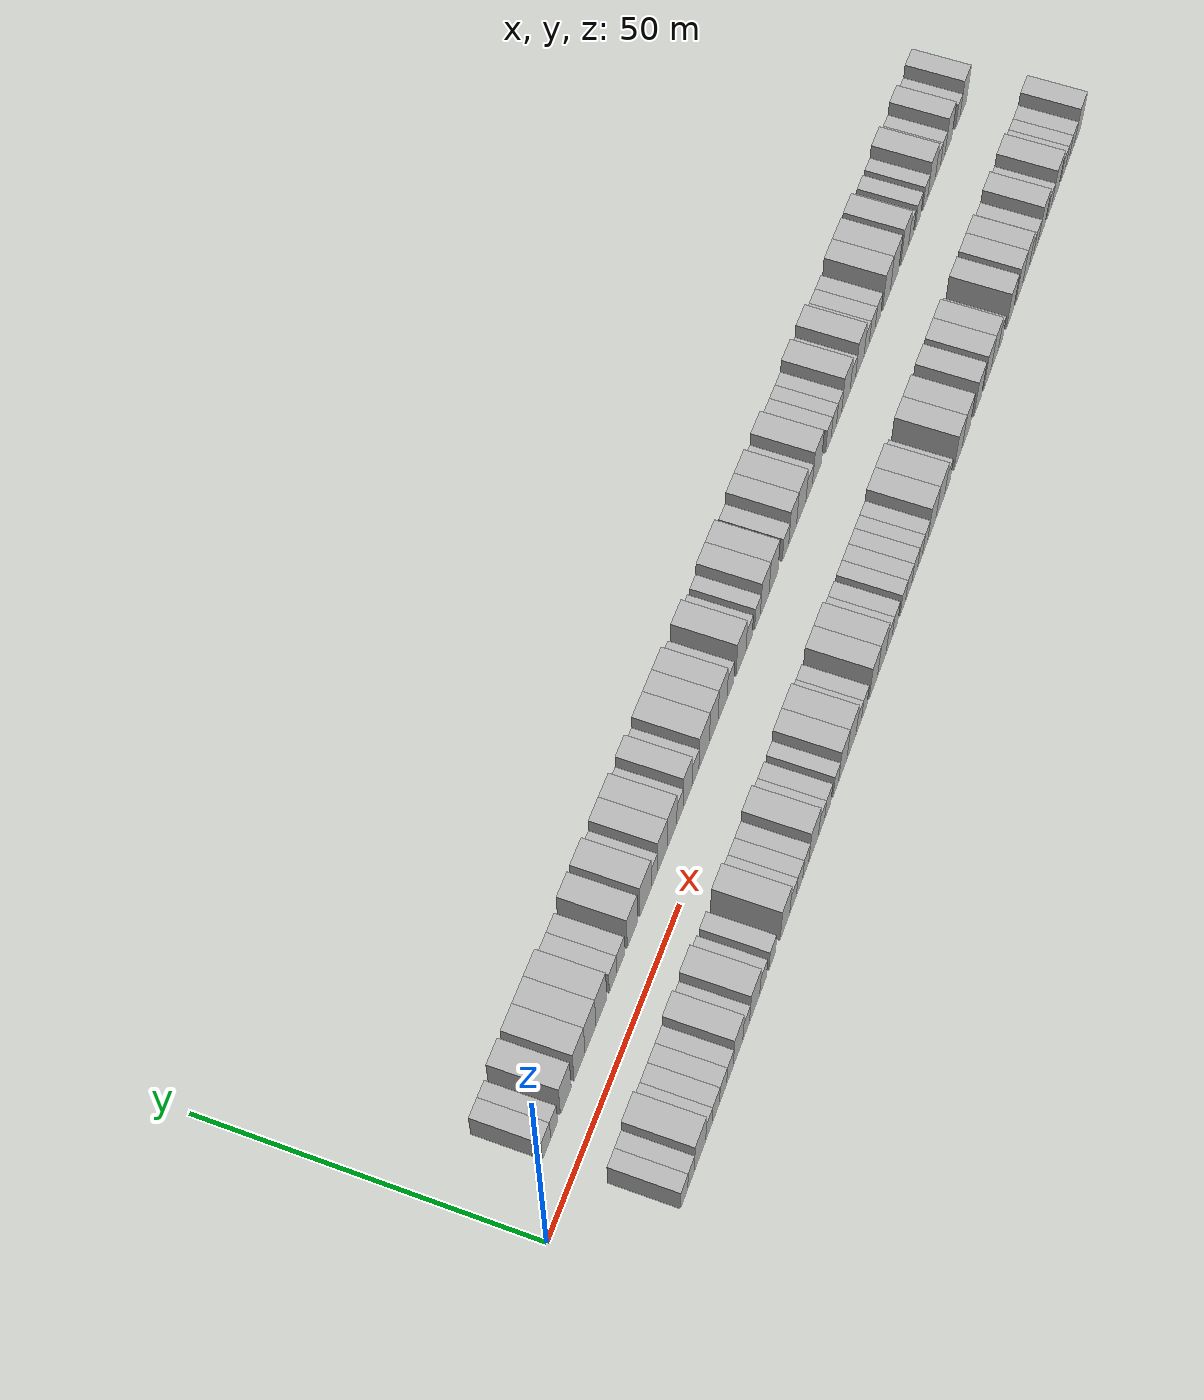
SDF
<sdf version="1.6">
 <world name="default">
  <scene>
   <sky><clouds><speed>12</speed></clouds></sky>
   <ambient>0.4 0.4 0.4 1</ambient>
   <background>0.7 0.7 0.7 1</background>
   <shadows>1</shadows>
  </scene>
  <gravity>0 0 -9.8066</gravity>
  <magnetic_field>6e-06 2.3e-05 -4.2e-05</magnetic_field>
  <physics default="0" name="default_physics" type="ode">
   <ode>
    <solver>
     <type>quick</type>
     <iters>10</iters>
     <sor>1.0</sor>
     <use_dynamic_moi_rescaling>0</use_dynamic_moi_rescaling>
    </solver>
    <constraints>
     <cfm>0</cfm>
     <erp>0.2</erp>
     <contact_max_correcting_vel>100</contact_max_correcting_vel>
     <contact_surface_layer>0.001</contact_surface_layer>
    </constraints>
   </ode>
   <max_step_size>0.004</max_step_size>
   <real_time_factor>1</real_time_factor>
   <real_time_update_rate>250</real_time_update_rate>
  </physics>
  <light name="sun" type="directional">
   <pose>0 0 10 0 0 0</pose>
   <diffuse>0.8 0.8 0.8 1</diffuse>
   <specular>0.2 0.2 0.2 1</specular>
   <attenuation>
    <range>1000</range>
    <constant>0.9</constant>
    <linear>0.01</linear>
    <quadratic>0.001</quadratic>
   </attenuation>
   <direction>-0.5 0.1 -0.9</direction>
  </light>
  <model name="building_1">
   <static>1</static>
   <pose>11.4937 9.5000 0 0.000000 0.000000 1.570796</pose>
   <link name="link">
    <pose>0 0 3.00 0 0 0</pose>
    <collision name="collision"><geometry><box><size>10.0000 2.9875 6.0000</size></box></geometry></collision>
    <visual name="visual">
     <cast_shadows>0</cast_shadows>
     <geometry><box><size>10.0000 2.9875 6.0000</size></box></geometry>
     <material>
      <script>
       <uri>model://HANNAS_wall/materials/scripts</uri>
       <uri>model://HANNAS_wall/materials/textures</uri>
       <name>vrc/HANNAS_wall</name>
      </script>
     </material>
    </visual>
   </link>
  </model>
  <model name="building_2">
   <static>1</static>
   <pose>14.2155 9.5000 0 0.000000 0.000000 1.570796</pose>
   <link name="link">
    <pose>0 0 3.00 0 0 0</pose>
    <collision name="collision"><geometry><box><size>10.0000 2.4561 6.0000</size></box></geometry></collision>
    <visual name="visual">
     <cast_shadows>0</cast_shadows>
     <geometry><box><size>10.0000 2.4561 6.0000</size></box></geometry>
     <material>
      <script>
       <uri>model://HANNAS_wall/materials/scripts</uri>
       <uri>model://HANNAS_wall/materials/textures</uri>
       <name>vrc/HANNAS_wall</name>
      </script>
     </material>
    </visual>
   </link>
  </model>
  <model name="building_3">
   <static>1</static>
   <pose>18.4167 9.5000 0 0.000000 0.000000 1.570796</pose>
   <link name="link">
    <pose>0 0 4.50 0 0 0</pose>
    <collision name="collision"><geometry><box><size>10.0000 3.9462 9.0000</size></box></geometry></collision>
    <visual name="visual">
     <cast_shadows>0</cast_shadows>
     <geometry><box><size>10.0000 3.9462 9.0000</size></box></geometry>
     <material>
      <script>
       <uri>model://HANNAS_wall/materials/scripts</uri>
       <uri>model://HANNAS_wall/materials/textures</uri>
       <name>vrc/HANNAS_wall</name>
      </script>
     </material>
    </visual>
   </link>
  </model>
  <model name="building_4">
   <static>1</static>
   <pose>23.4204 9.5000 0 0.000000 0.000000 1.570796</pose>
   <link name="link">
    <pose>0 0 4.50 0 0 0</pose>
    <collision name="collision"><geometry><box><size>10.0000 4.0612 9.0000</size></box></geometry></collision>
    <visual name="visual">
     <cast_shadows>0</cast_shadows>
     <geometry><box><size>10.0000 4.0612 9.0000</size></box></geometry>
     <material>
      <script>
       <uri>model://HANNAS_wall/materials/scripts</uri>
       <uri>model://HANNAS_wall/materials/textures</uri>
       <name>vrc/HANNAS_wall</name>
      </script>
     </material>
    </visual>
   </link>
  </model>
  <model name="building_5">
   <static>1</static>
   <pose>27.4896 9.5000 0 0.000000 0.000000 1.570796</pose>
   <link name="link">
    <pose>0 0 4.50 0 0 0</pose>
    <collision name="collision"><geometry><box><size>10.0000 4.0774 9.0000</size></box></geometry></collision>
    <visual name="visual">
     <cast_shadows>0</cast_shadows>
     <geometry><box><size>10.0000 4.0774 9.0000</size></box></geometry>
     <material>
      <script>
       <uri>model://HANNAS_wall/materials/scripts</uri>
       <uri>model://HANNAS_wall/materials/textures</uri>
       <name>vrc/HANNAS_wall</name>
      </script>
     </material>
    </visual>
   </link>
  </model>
  <model name="building_6">
   <static>1</static>
   <pose>31.5653 9.5000 0 0.000000 0.000000 1.570796</pose>
   <link name="link">
    <pose>0 0 4.50 0 0 0</pose>
    <collision name="collision"><geometry><box><size>10.0000 4.0740 9.0000</size></box></geometry></collision>
    <visual name="visual">
     <cast_shadows>0</cast_shadows>
     <geometry><box><size>10.0000 4.0740 9.0000</size></box></geometry>
     <material>
      <script>
       <uri>model://HANNAS_wall/materials/scripts</uri>
       <uri>model://HANNAS_wall/materials/textures</uri>
       <name>vrc/HANNAS_wall</name>
      </script>
     </material>
    </visual>
   </link>
  </model>
  <model name="building_7">
   <static>1</static>
   <pose>36.0594 9.5000 0 0.000000 0.000000 1.570796</pose>
   <link name="link">
    <pose>0 0 3.00 0 0 0</pose>
    <collision name="collision"><geometry><box><size>10.0000 2.9140 6.0000</size></box></geometry></collision>
    <visual name="visual">
     <cast_shadows>0</cast_shadows>
     <geometry><box><size>10.0000 2.9140 6.0000</size></box></geometry>
     <material>
      <script>
       <uri>model://HANNAS_wall/materials/scripts</uri>
       <uri>model://HANNAS_wall/materials/textures</uri>
       <name>vrc/HANNAS_wall</name>
      </script>
     </material>
    </visual>
   </link>
  </model>
  <model name="building_8">
   <static>1</static>
   <pose>38.9993 9.5000 0 0.000000 0.000000 1.570796</pose>
   <link name="link">
    <pose>0 0 3.00 0 0 0</pose>
    <collision name="collision"><geometry><box><size>10.0000 2.9658 6.0000</size></box></geometry></collision>
    <visual name="visual">
     <cast_shadows>0</cast_shadows>
     <geometry><box><size>10.0000 2.9658 6.0000</size></box></geometry>
     <material>
      <script>
       <uri>model://HANNAS_wall/materials/scripts</uri>
       <uri>model://HANNAS_wall/materials/textures</uri>
       <name>vrc/HANNAS_wall</name>
      </script>
     </material>
    </visual>
   </link>
  </model>
  <model name="building_9">
   <static>1</static>
   <pose>43.4593 9.5000 0 0.000000 0.000000 1.570796</pose>
   <link name="link">
    <pose>0 0 4.50 0 0 0</pose>
    <collision name="collision"><geometry><box><size>10.0000 3.9543 9.0000</size></box></geometry></collision>
    <visual name="visual">
     <cast_shadows>0</cast_shadows>
     <geometry><box><size>10.0000 3.9543 9.0000</size></box></geometry>
     <material>
      <script>
       <uri>model://HANNAS_wall/materials/scripts</uri>
       <uri>model://HANNAS_wall/materials/textures</uri>
       <name>vrc/HANNAS_wall</name>
      </script>
     </material>
    </visual>
   </link>
  </model>
  <model name="building_10">
   <static>1</static>
   <pose>48.6359 9.5000 0 0.000000 0.000000 1.570796</pose>
   <link name="link">
    <pose>0 0 4.50 0 0 0</pose>
    <collision name="collision"><geometry><box><size>10.0000 4.3989 9.0000</size></box></geometry></collision>
    <visual name="visual">
     <cast_shadows>0</cast_shadows>
     <geometry><box><size>10.0000 4.3989 9.0000</size></box></geometry>
     <material>
      <script>
       <uri>model://HANNAS_wall/materials/scripts</uri>
       <uri>model://HANNAS_wall/materials/textures</uri>
       <name>vrc/HANNAS_wall</name>
      </script>
     </material>
    </visual>
   </link>
  </model>
  <model name="building_11">
   <static>1</static>
   <pose>52.1533 9.5000 0 0.000000 0.000000 1.570796</pose>
   <link name="link">
    <pose>0 0 3.00 0 0 0</pose>
    <collision name="collision"><geometry><box><size>10.0000 2.6358 6.0000</size></box></geometry></collision>
    <visual name="visual">
     <cast_shadows>0</cast_shadows>
     <geometry><box><size>10.0000 2.6358 6.0000</size></box></geometry>
     <material>
      <script>
       <uri>model://HANNAS_wall/materials/scripts</uri>
       <uri>model://HANNAS_wall/materials/textures</uri>
       <name>vrc/HANNAS_wall</name>
      </script>
     </material>
    </visual>
   </link>
  </model>
  <model name="building_12">
   <static>1</static>
   <pose>55.3849 9.5000 0 0.000000 0.000000 1.570796</pose>
   <link name="link">
    <pose>0 0 4.50 0 0 0</pose>
    <collision name="collision"><geometry><box><size>10.0000 3.8273 9.0000</size></box></geometry></collision>
    <visual name="visual">
     <cast_shadows>0</cast_shadows>
     <geometry><box><size>10.0000 3.8273 9.0000</size></box></geometry>
     <material>
      <script>
       <uri>model://HANNAS_wall/materials/scripts</uri>
       <uri>model://HANNAS_wall/materials/textures</uri>
       <name>vrc/HANNAS_wall</name>
      </script>
     </material>
    </visual>
   </link>
  </model>
  <model name="building_13">
   <static>1</static>
   <pose>59.2486 9.5000 0 0.000000 0.000000 1.570796</pose>
   <link name="link">
    <pose>0 0 4.50 0 0 0</pose>
    <collision name="collision"><geometry><box><size>10.0000 3.9002 9.0000</size></box></geometry></collision>
    <visual name="visual">
     <cast_shadows>0</cast_shadows>
     <geometry><box><size>10.0000 3.9002 9.0000</size></box></geometry>
     <material>
      <script>
       <uri>model://HANNAS_wall/materials/scripts</uri>
       <uri>model://HANNAS_wall/materials/textures</uri>
       <name>vrc/HANNAS_wall</name>
      </script>
     </material>
    </visual>
   </link>
  </model>
  <model name="building_14">
   <static>1</static>
   <pose>62.5120 9.5000 0 0.000000 0.000000 1.570796</pose>
   <link name="link">
    <pose>0 0 3.00 0 0 0</pose>
    <collision name="collision"><geometry><box><size>10.0000 2.6267 6.0000</size></box></geometry></collision>
    <visual name="visual">
     <cast_shadows>0</cast_shadows>
     <geometry><box><size>10.0000 2.6267 6.0000</size></box></geometry>
     <material>
      <script>
       <uri>model://HANNAS_wall/materials/scripts</uri>
       <uri>model://HANNAS_wall/materials/textures</uri>
       <name>vrc/HANNAS_wall</name>
      </script>
     </material>
    </visual>
   </link>
  </model>
  <model name="building_15">
   <static>1</static>
   <pose>65.6415 9.5000 0 0.000000 0.000000 1.570796</pose>
   <link name="link">
    <pose>0 0 4.50 0 0 0</pose>
    <collision name="collision"><geometry><box><size>10.0000 3.6323 9.0000</size></box></geometry></collision>
    <visual name="visual">
     <cast_shadows>0</cast_shadows>
     <geometry><box><size>10.0000 3.6323 9.0000</size></box></geometry>
     <material>
      <script>
       <uri>model://HANNAS_wall/materials/scripts</uri>
       <uri>model://HANNAS_wall/materials/textures</uri>
       <name>vrc/HANNAS_wall</name>
      </script>
     </material>
    </visual>
   </link>
  </model>
  <model name="building_16">
   <static>1</static>
   <pose>68.8954 9.5000 0 0.000000 0.000000 1.570796</pose>
   <link name="link">
    <pose>0 0 3.00 0 0 0</pose>
    <collision name="collision"><geometry><box><size>10.0000 2.8755 6.0000</size></box></geometry></collision>
    <visual name="visual">
     <cast_shadows>0</cast_shadows>
     <geometry><box><size>10.0000 2.8755 6.0000</size></box></geometry>
     <material>
      <script>
       <uri>model://HANNAS_wall/materials/scripts</uri>
       <uri>model://HANNAS_wall/materials/textures</uri>
       <name>vrc/HANNAS_wall</name>
      </script>
     </material>
    </visual>
   </link>
  </model>
  <model name="building_17">
   <static>1</static>
   <pose>72.5236 9.5000 0 0.000000 0.000000 1.570796</pose>
   <link name="link">
    <pose>0 0 4.50 0 0 0</pose>
    <collision name="collision"><geometry><box><size>10.0000 4.3809 9.0000</size></box></geometry></collision>
    <visual name="visual">
     <cast_shadows>0</cast_shadows>
     <geometry><box><size>10.0000 4.3809 9.0000</size></box></geometry>
     <material>
      <script>
       <uri>model://HANNAS_wall/materials/scripts</uri>
       <uri>model://HANNAS_wall/materials/textures</uri>
       <name>vrc/HANNAS_wall</name>
      </script>
     </material>
    </visual>
   </link>
  </model>
  <model name="building_18">
   <static>1</static>
   <pose>76.5592 9.5000 0 0.000000 0.000000 1.570796</pose>
   <link name="link">
    <pose>0 0 4.50 0 0 0</pose>
    <collision name="collision"><geometry><box><size>10.0000 3.6902 9.0000</size></box></geometry></collision>
    <visual name="visual">
     <cast_shadows>0</cast_shadows>
     <geometry><box><size>10.0000 3.6902 9.0000</size></box></geometry>
     <material>
      <script>
       <uri>model://HANNAS_wall/materials/scripts</uri>
       <uri>model://HANNAS_wall/materials/textures</uri>
       <name>vrc/HANNAS_wall</name>
      </script>
     </material>
    </visual>
   </link>
  </model>
  <model name="building_19">
   <static>1</static>
   <pose>80.3442 9.5000 0 0.000000 0.000000 1.570796</pose>
   <link name="link">
    <pose>0 0 4.50 0 0 0</pose>
    <collision name="collision"><geometry><box><size>10.0000 3.8799 9.0000</size></box></geometry></collision>
    <visual name="visual">
     <cast_shadows>0</cast_shadows>
     <geometry><box><size>10.0000 3.8799 9.0000</size></box></geometry>
     <material>
      <script>
       <uri>model://HANNAS_wall/materials/scripts</uri>
       <uri>model://HANNAS_wall/materials/textures</uri>
       <name>vrc/HANNAS_wall</name>
      </script>
     </material>
    </visual>
   </link>
  </model>
  <model name="building_20">
   <static>1</static>
   <pose>83.7181 9.5000 0 0.000000 0.000000 1.570796</pose>
   <link name="link">
    <pose>0 0 3.00 0 0 0</pose>
    <collision name="collision"><geometry><box><size>10.0000 2.8679 6.0000</size></box></geometry></collision>
    <visual name="visual">
     <cast_shadows>0</cast_shadows>
     <geometry><box><size>10.0000 2.8679 6.0000</size></box></geometry>
     <material>
      <script>
       <uri>model://HANNAS_wall/materials/scripts</uri>
       <uri>model://HANNAS_wall/materials/textures</uri>
       <name>vrc/HANNAS_wall</name>
      </script>
     </material>
    </visual>
   </link>
  </model>
  <model name="building_21">
   <static>1</static>
   <pose>88.3135 9.5000 0 0.000000 0.000000 1.570796</pose>
   <link name="link">
    <pose>0 0 4.50 0 0 0</pose>
    <collision name="collision"><geometry><box><size>10.0000 4.3228 9.0000</size></box></geometry></collision>
    <visual name="visual">
     <cast_shadows>0</cast_shadows>
     <geometry><box><size>10.0000 4.3228 9.0000</size></box></geometry>
     <material>
      <script>
       <uri>model://HANNAS_wall/materials/scripts</uri>
       <uri>model://HANNAS_wall/materials/textures</uri>
       <name>vrc/HANNAS_wall</name>
      </script>
     </material>
    </visual>
   </link>
  </model>
  <model name="building_22">
   <static>1</static>
   <pose>91.8621 9.5000 0 0.000000 0.000000 1.570796</pose>
   <link name="link">
    <pose>0 0 3.00 0 0 0</pose>
    <collision name="collision"><geometry><box><size>10.0000 2.7743 6.0000</size></box></geometry></collision>
    <visual name="visual">
     <cast_shadows>0</cast_shadows>
     <geometry><box><size>10.0000 2.7743 6.0000</size></box></geometry>
     <material>
      <script>
       <uri>model://HANNAS_wall/materials/scripts</uri>
       <uri>model://HANNAS_wall/materials/textures</uri>
       <name>vrc/HANNAS_wall</name>
      </script>
     </material>
    </visual>
   </link>
  </model>
  <model name="building_23">
   <static>1</static>
   <pose>95.5293 9.5000 0 0.000000 0.000000 1.570796</pose>
   <link name="link">
    <pose>0 0 3.00 0 0 0</pose>
    <collision name="collision"><geometry><box><size>10.0000 2.5601 6.0000</size></box></geometry></collision>
    <visual name="visual">
     <cast_shadows>0</cast_shadows>
     <geometry><box><size>10.0000 2.5601 6.0000</size></box></geometry>
     <material>
      <script>
       <uri>model://HANNAS_wall/materials/scripts</uri>
       <uri>model://HANNAS_wall/materials/textures</uri>
       <name>vrc/HANNAS_wall</name>
      </script>
     </material>
    </visual>
   </link>
  </model>
  <model name="building_24">
   <static>1</static>
   <pose>98.7638 9.5000 0 0.000000 0.000000 1.570796</pose>
   <link name="link">
    <pose>0 0 4.50 0 0 0</pose>
    <collision name="collision"><geometry><box><size>10.0000 3.9090 9.0000</size></box></geometry></collision>
    <visual name="visual">
     <cast_shadows>0</cast_shadows>
     <geometry><box><size>10.0000 3.9090 9.0000</size></box></geometry>
     <material>
      <script>
       <uri>model://HANNAS_wall/materials/scripts</uri>
       <uri>model://HANNAS_wall/materials/textures</uri>
       <name>vrc/HANNAS_wall</name>
      </script>
     </material>
    </visual>
   </link>
  </model>
  <model name="building_25">
   <static>1</static>
   <pose>102.7310 9.5000 0 0.000000 0.000000 1.570796</pose>
   <link name="link">
    <pose>0 0 4.50 0 0 0</pose>
    <collision name="collision"><geometry><box><size>10.0000 4.0255 9.0000</size></box></geometry></collision>
    <visual name="visual">
     <cast_shadows>0</cast_shadows>
     <geometry><box><size>10.0000 4.0255 9.0000</size></box></geometry>
     <material>
      <script>
       <uri>model://HANNAS_wall/materials/scripts</uri>
       <uri>model://HANNAS_wall/materials/textures</uri>
       <name>vrc/HANNAS_wall</name>
      </script>
     </material>
    </visual>
   </link>
  </model>
  <model name="building_26">
   <static>1</static>
   <pose>108.1972 9.5000 0 0.000000 0.000000 1.570796</pose>
   <link name="link">
    <pose>0 0 3.00 0 0 0</pose>
    <collision name="collision"><geometry><box><size>10.0000 2.9069 6.0000</size></box></geometry></collision>
    <visual name="visual">
     <cast_shadows>0</cast_shadows>
     <geometry><box><size>10.0000 2.9069 6.0000</size></box></geometry>
     <material>
      <script>
       <uri>model://HANNAS_wall/materials/scripts</uri>
       <uri>model://HANNAS_wall/materials/textures</uri>
       <name>vrc/HANNAS_wall</name>
      </script>
     </material>
    </visual>
   </link>
  </model>
  <model name="building_27">
   <static>1</static>
   <pose>111.4768 9.5000 0 0.000000 0.000000 1.570796</pose>
   <link name="link">
    <pose>0 0 4.50 0 0 0</pose>
    <collision name="collision"><geometry><box><size>10.0000 3.6522 9.0000</size></box></geometry></collision>
    <visual name="visual">
     <cast_shadows>0</cast_shadows>
     <geometry><box><size>10.0000 3.6522 9.0000</size></box></geometry>
     <material>
      <script>
       <uri>model://HANNAS_wall/materials/scripts</uri>
       <uri>model://HANNAS_wall/materials/textures</uri>
       <name>vrc/HANNAS_wall</name>
      </script>
     </material>
    </visual>
   </link>
  </model>
  <model name="building_28">
   <static>1</static>
   <pose>115.4859 9.5000 0 0.000000 0.000000 1.570796</pose>
   <link name="link">
    <pose>0 0 4.50 0 0 0</pose>
    <collision name="collision"><geometry><box><size>10.0000 4.3660 9.0000</size></box></geometry></collision>
    <visual name="visual">
     <cast_shadows>0</cast_shadows>
     <geometry><box><size>10.0000 4.3660 9.0000</size></box></geometry>
     <material>
      <script>
       <uri>model://HANNAS_wall/materials/scripts</uri>
       <uri>model://HANNAS_wall/materials/textures</uri>
       <name>vrc/HANNAS_wall</name>
      </script>
     </material>
    </visual>
   </link>
  </model>
  <model name="building_29">
   <static>1</static>
   <pose>119.1669 9.5000 0 0.000000 0.000000 1.570796</pose>
   <link name="link">
    <pose>0 0 3.00 0 0 0</pose>
    <collision name="collision"><geometry><box><size>10.0000 2.9960 6.0000</size></box></geometry></collision>
    <visual name="visual">
     <cast_shadows>0</cast_shadows>
     <geometry><box><size>10.0000 2.9960 6.0000</size></box></geometry>
     <material>
      <script>
       <uri>model://HANNAS_wall/materials/scripts</uri>
       <uri>model://HANNAS_wall/materials/textures</uri>
       <name>vrc/HANNAS_wall</name>
      </script>
     </material>
    </visual>
   </link>
  </model>
  <model name="building_30">
   <static>1</static>
   <pose>122.8163 9.5000 0 0.000000 0.000000 1.570796</pose>
   <link name="link">
    <pose>0 0 4.50 0 0 0</pose>
    <collision name="collision"><geometry><box><size>10.0000 4.3029 9.0000</size></box></geometry></collision>
    <visual name="visual">
     <cast_shadows>0</cast_shadows>
     <geometry><box><size>10.0000 4.3029 9.0000</size></box></geometry>
     <material>
      <script>
       <uri>model://HANNAS_wall/materials/scripts</uri>
       <uri>model://HANNAS_wall/materials/textures</uri>
       <name>vrc/HANNAS_wall</name>
      </script>
     </material>
    </visual>
   </link>
  </model>
  <model name="building_31">
   <static>1</static>
   <pose>128.2900 9.5000 0 0.000000 0.000000 1.570796</pose>
   <link name="link">
    <pose>0 0 3.00 0 0 0</pose>
    <collision name="collision"><geometry><box><size>10.0000 2.6445 6.0000</size></box></geometry></collision>
    <visual name="visual">
     <cast_shadows>0</cast_shadows>
     <geometry><box><size>10.0000 2.6445 6.0000</size></box></geometry>
     <material>
      <script>
       <uri>model://HANNAS_wall/materials/scripts</uri>
       <uri>model://HANNAS_wall/materials/textures</uri>
       <name>vrc/HANNAS_wall</name>
      </script>
     </material>
    </visual>
   </link>
  </model>
  <model name="building_32">
   <static>1</static>
   <pose>130.9138 9.5000 0 0.000000 0.000000 1.570796</pose>
   <link name="link">
    <pose>0 0 3.00 0 0 0</pose>
    <collision name="collision"><geometry><box><size>10.0000 2.6032 6.0000</size></box></geometry></collision>
    <visual name="visual">
     <cast_shadows>0</cast_shadows>
     <geometry><box><size>10.0000 2.6032 6.0000</size></box></geometry>
     <material>
      <script>
       <uri>model://HANNAS_wall/materials/scripts</uri>
       <uri>model://HANNAS_wall/materials/textures</uri>
       <name>vrc/HANNAS_wall</name>
      </script>
     </material>
    </visual>
   </link>
  </model>
  <model name="building_33">
   <static>1</static>
   <pose>133.4802 9.5000 0 0.000000 0.000000 1.570796</pose>
   <link name="link">
    <pose>0 0 3.00 0 0 0</pose>
    <collision name="collision"><geometry><box><size>10.0000 2.5295 6.0000</size></box></geometry></collision>
    <visual name="visual">
     <cast_shadows>0</cast_shadows>
     <geometry><box><size>10.0000 2.5295 6.0000</size></box></geometry>
     <material>
      <script>
       <uri>model://HANNAS_wall/materials/scripts</uri>
       <uri>model://HANNAS_wall/materials/textures</uri>
       <name>vrc/HANNAS_wall</name>
      </script>
     </material>
    </visual>
   </link>
  </model>
  <model name="building_34">
   <static>1</static>
   <pose>136.8274 9.5000 0 0.000000 0.000000 1.570796</pose>
   <link name="link">
    <pose>0 0 4.50 0 0 0</pose>
    <collision name="collision"><geometry><box><size>10.0000 4.1649 9.0000</size></box></geometry></collision>
    <visual name="visual">
     <cast_shadows>0</cast_shadows>
     <geometry><box><size>10.0000 4.1649 9.0000</size></box></geometry>
     <material>
      <script>
       <uri>model://HANNAS_wall/materials/scripts</uri>
       <uri>model://HANNAS_wall/materials/textures</uri>
       <name>vrc/HANNAS_wall</name>
      </script>
     </material>
    </visual>
   </link>
  </model>
  <model name="building_35">
   <static>1</static>
   <pose>140.2510 9.5000 0 0.000000 0.000000 1.570796</pose>
   <link name="link">
    <pose>0 0 3.00 0 0 0</pose>
    <collision name="collision"><geometry><box><size>10.0000 2.6823 6.0000</size></box></geometry></collision>
    <visual name="visual">
     <cast_shadows>0</cast_shadows>
     <geometry><box><size>10.0000 2.6823 6.0000</size></box></geometry>
     <material>
      <script>
       <uri>model://HANNAS_wall/materials/scripts</uri>
       <uri>model://HANNAS_wall/materials/textures</uri>
       <name>vrc/HANNAS_wall</name>
      </script>
     </material>
    </visual>
   </link>
  </model>
  <model name="building_36">
   <static>1</static>
   <pose>143.6813 9.5000 0 0.000000 0.000000 1.570796</pose>
   <link name="link">
    <pose>0 0 4.50 0 0 0</pose>
    <collision name="collision"><geometry><box><size>10.0000 4.1784 9.0000</size></box></geometry></collision>
    <visual name="visual">
     <cast_shadows>0</cast_shadows>
     <geometry><box><size>10.0000 4.1784 9.0000</size></box></geometry>
     <material>
      <script>
       <uri>model://HANNAS_wall/materials/scripts</uri>
       <uri>model://HANNAS_wall/materials/textures</uri>
       <name>vrc/HANNAS_wall</name>
      </script>
     </material>
    </visual>
   </link>
  </model>
  <model name="building_37">
   <static>1</static>
   <pose>147.1020 9.5000 0 0.000000 0.000000 1.570796</pose>
   <link name="link">
    <pose>0 0 3.00 0 0 0</pose>
    <collision name="collision"><geometry><box><size>10.0000 2.6631 6.0000</size></box></geometry></collision>
    <visual name="visual">
     <cast_shadows>0</cast_shadows>
     <geometry><box><size>10.0000 2.6631 6.0000</size></box></geometry>
     <material>
      <script>
       <uri>model://HANNAS_wall/materials/scripts</uri>
       <uri>model://HANNAS_wall/materials/textures</uri>
       <name>vrc/HANNAS_wall</name>
      </script>
     </material>
    </visual>
   </link>
  </model>
  <model name="building_38">
   <static>1</static>
   <pose>149.8932 9.5000 0 0.000000 0.000000 1.570796</pose>
   <link name="link">
    <pose>0 0 3.00 0 0 0</pose>
    <collision name="collision"><geometry><box><size>10.0000 2.9192 6.0000</size></box></geometry></collision>
    <visual name="visual">
     <cast_shadows>0</cast_shadows>
     <geometry><box><size>10.0000 2.9192 6.0000</size></box></geometry>
     <material>
      <script>
       <uri>model://HANNAS_wall/materials/scripts</uri>
       <uri>model://HANNAS_wall/materials/textures</uri>
       <name>vrc/HANNAS_wall</name>
      </script>
     </material>
    </visual>
   </link>
  </model>
  <model name="building_39">
   <static>1</static>
   <pose>152.7560 9.5000 0 0.000000 0.000000 1.570796</pose>
   <link name="link">
    <pose>0 0 3.00 0 0 0</pose>
    <collision name="collision"><geometry><box><size>10.0000 2.8065 6.0000</size></box></geometry></collision>
    <visual name="visual">
     <cast_shadows>0</cast_shadows>
     <geometry><box><size>10.0000 2.8065 6.0000</size></box></geometry>
     <material>
      <script>
       <uri>model://HANNAS_wall/materials/scripts</uri>
       <uri>model://HANNAS_wall/materials/textures</uri>
       <name>vrc/HANNAS_wall</name>
      </script>
     </material>
    </visual>
   </link>
  </model>
  <model name="building_40">
   <static>1</static>
   <pose>157.1732 9.5000 0 0.000000 0.000000 1.570796</pose>
   <link name="link">
    <pose>0 0 4.50 0 0 0</pose>
    <collision name="collision"><geometry><box><size>10.0000 4.0280 9.0000</size></box></geometry></collision>
    <visual name="visual">
     <cast_shadows>0</cast_shadows>
     <geometry><box><size>10.0000 4.0280 9.0000</size></box></geometry>
     <material>
      <script>
       <uri>model://HANNAS_wall/materials/scripts</uri>
       <uri>model://HANNAS_wall/materials/textures</uri>
       <name>vrc/HANNAS_wall</name>
      </script>
     </material>
    </visual>
   </link>
  </model>
  <model name="building_41">
   <static>1</static>
   <pose>161.3791 9.5000 0 0.000000 0.000000 1.570796</pose>
   <link name="link">
    <pose>0 0 4.50 0 0 0</pose>
    <collision name="collision"><geometry><box><size>10.0000 4.3838 9.0000</size></box></geometry></collision>
    <visual name="visual">
     <cast_shadows>0</cast_shadows>
     <geometry><box><size>10.0000 4.3838 9.0000</size></box></geometry>
     <material>
      <script>
       <uri>model://HANNAS_wall/materials/scripts</uri>
       <uri>model://HANNAS_wall/materials/textures</uri>
       <name>vrc/HANNAS_wall</name>
      </script>
     </material>
    </visual>
   </link>
  </model>
  <model name="building_42">
   <static>1</static>
   <pose>166.6111 9.5000 0 0.000000 0.000000 1.570796</pose>
   <link name="link">
    <pose>0 0 4.50 0 0 0</pose>
    <collision name="collision"><geometry><box><size>10.0000 4.0802 9.0000</size></box></geometry></collision>
    <visual name="visual">
     <cast_shadows>0</cast_shadows>
     <geometry><box><size>10.0000 4.0802 9.0000</size></box></geometry>
     <material>
      <script>
       <uri>model://HANNAS_wall/materials/scripts</uri>
       <uri>model://HANNAS_wall/materials/textures</uri>
       <name>vrc/HANNAS_wall</name>
      </script>
     </material>
    </visual>
   </link>
  </model>
  <model name="building_43">
   <static>1</static>
   <pose>169.9152 9.5000 0 0.000000 0.000000 1.570796</pose>
   <link name="link">
    <pose>0 0 3.00 0 0 0</pose>
    <collision name="collision"><geometry><box><size>10.0000 2.5280 6.0000</size></box></geometry></collision>
    <visual name="visual">
     <cast_shadows>0</cast_shadows>
     <geometry><box><size>10.0000 2.5280 6.0000</size></box></geometry>
     <material>
      <script>
       <uri>model://HANNAS_wall/materials/scripts</uri>
       <uri>model://HANNAS_wall/materials/textures</uri>
       <name>vrc/HANNAS_wall</name>
      </script>
     </material>
    </visual>
   </link>
  </model>
  <model name="building_44">
   <static>1</static>
   <pose>173.6654 9.5000 0 0.000000 0.000000 1.570796</pose>
   <link name="link">
    <pose>0 0 3.00 0 0 0</pose>
    <collision name="collision"><geometry><box><size>10.0000 2.9724 6.0000</size></box></geometry></collision>
    <visual name="visual">
     <cast_shadows>0</cast_shadows>
     <geometry><box><size>10.0000 2.9724 6.0000</size></box></geometry>
     <material>
      <script>
       <uri>model://HANNAS_wall/materials/scripts</uri>
       <uri>model://HANNAS_wall/materials/textures</uri>
       <name>vrc/HANNAS_wall</name>
      </script>
     </material>
    </visual>
   </link>
  </model>
  <model name="building_45">
   <static>1</static>
   <pose>177.4917 9.5000 0 0.000000 0.000000 1.570796</pose>
   <link name="link">
    <pose>0 0 3.00 0 0 0</pose>
    <collision name="collision"><geometry><box><size>10.0000 2.6803 6.0000</size></box></geometry></collision>
    <visual name="visual">
     <cast_shadows>0</cast_shadows>
     <geometry><box><size>10.0000 2.6803 6.0000</size></box></geometry>
     <material>
      <script>
       <uri>model://HANNAS_wall/materials/scripts</uri>
       <uri>model://HANNAS_wall/materials/textures</uri>
       <name>vrc/HANNAS_wall</name>
      </script>
     </material>
    </visual>
   </link>
  </model>
  <model name="building_46">
   <static>1</static>
   <pose>180.9124 9.5000 0 0.000000 0.000000 1.570796</pose>
   <link name="link">
    <pose>0 0 4.50 0 0 0</pose>
    <collision name="collision"><geometry><box><size>10.0000 4.1611 9.0000</size></box></geometry></collision>
    <visual name="visual">
     <cast_shadows>0</cast_shadows>
     <geometry><box><size>10.0000 4.1611 9.0000</size></box></geometry>
     <material>
      <script>
       <uri>model://HANNAS_wall/materials/scripts</uri>
       <uri>model://HANNAS_wall/materials/textures</uri>
       <name>vrc/HANNAS_wall</name>
      </script>
     </material>
    </visual>
   </link>
  </model>
  <model name="building_47">
   <static>1</static>
   <pose>184.4054 9.5000 0 0.000000 0.000000 1.570796</pose>
   <link name="link">
    <pose>0 0 3.00 0 0 0</pose>
    <collision name="collision"><geometry><box><size>10.0000 2.8249 6.0000</size></box></geometry></collision>
    <visual name="visual">
     <cast_shadows>0</cast_shadows>
     <geometry><box><size>10.0000 2.8249 6.0000</size></box></geometry>
     <material>
      <script>
       <uri>model://HANNAS_wall/materials/scripts</uri>
       <uri>model://HANNAS_wall/materials/textures</uri>
       <name>vrc/HANNAS_wall</name>
      </script>
     </material>
    </visual>
   </link>
  </model>
  <model name="building_48">
   <static>1</static>
   <pose>187.0541 9.5000 0 0.000000 0.000000 1.570796</pose>
   <link name="link">
    <pose>0 0 3.00 0 0 0</pose>
    <collision name="collision"><geometry><box><size>10.0000 2.4724 6.0000</size></box></geometry></collision>
    <visual name="visual">
     <cast_shadows>0</cast_shadows>
     <geometry><box><size>10.0000 2.4724 6.0000</size></box></geometry>
     <material>
      <script>
       <uri>model://HANNAS_wall/materials/scripts</uri>
       <uri>model://HANNAS_wall/materials/textures</uri>
       <name>vrc/HANNAS_wall</name>
      </script>
     </material>
    </visual>
   </link>
  </model>
  <model name="building_49">
   <static>1</static>
   <pose>190.1985 9.5000 0 0.000000 0.000000 1.570796</pose>
   <link name="link">
    <pose>0 0 4.50 0 0 0</pose>
    <collision name="collision"><geometry><box><size>10.0000 3.8163 9.0000</size></box></geometry></collision>
    <visual name="visual">
     <cast_shadows>0</cast_shadows>
     <geometry><box><size>10.0000 3.8163 9.0000</size></box></geometry>
     <material>
      <script>
       <uri>model://HANNAS_wall/materials/scripts</uri>
       <uri>model://HANNAS_wall/materials/textures</uri>
       <name>vrc/HANNAS_wall</name>
      </script>
     </material>
    </visual>
   </link>
  </model>
  <model name="building_50">
   <static>1</static>
   <pose>195.3484 9.5000 0 0.000000 0.000000 1.570796</pose>
   <link name="link">
    <pose>0 0 3.00 0 0 0</pose>
    <collision name="collision"><geometry><box><size>10.0000 2.4836 6.0000</size></box></geometry></collision>
    <visual name="visual">
     <cast_shadows>0</cast_shadows>
     <geometry><box><size>10.0000 2.4836 6.0000</size></box></geometry>
     <material>
      <script>
       <uri>model://HANNAS_wall/materials/scripts</uri>
       <uri>model://HANNAS_wall/materials/textures</uri>
       <name>vrc/HANNAS_wall</name>
      </script>
     </material>
    </visual>
   </link>
  </model>
  <model name="building_51">
   <static>1</static>
   <pose>198.4398 9.5000 0 0.000000 0.000000 1.570796</pose>
   <link name="link">
    <pose>0 0 4.50 0 0 0</pose>
    <collision name="collision"><geometry><box><size>10.0000 3.6991 9.0000</size></box></geometry></collision>
    <visual name="visual">
     <cast_shadows>0</cast_shadows>
     <geometry><box><size>10.0000 3.6991 9.0000</size></box></geometry>
     <material>
      <script>
       <uri>model://HANNAS_wall/materials/scripts</uri>
       <uri>model://HANNAS_wall/materials/textures</uri>
       <name>vrc/HANNAS_wall</name>
      </script>
     </material>
    </visual>
   </link>
  </model>
  <model name="building_52">
   <static>1</static>
   <pose>11.3659 -9.5000 0 0.000000 0.000000 1.570796</pose>
   <link name="link">
    <pose>0 0 3.00 0 0 0</pose>
    <collision name="collision"><geometry><box><size>10.0000 2.7319 6.0000</size></box></geometry></collision>
    <visual name="visual">
     <cast_shadows>0</cast_shadows>
     <geometry><box><size>10.0000 2.7319 6.0000</size></box></geometry>
     <material>
      <script>
       <uri>model://HANNAS_wall/materials/scripts</uri>
       <uri>model://HANNAS_wall/materials/textures</uri>
       <name>vrc/HANNAS_wall</name>
      </script>
     </material>
    </visual>
   </link>
  </model>
  <model name="building_53">
   <static>1</static>
   <pose>13.9911 -9.5000 0 0.000000 0.000000 1.570796</pose>
   <link name="link">
    <pose>0 0 3.00 0 0 0</pose>
    <collision name="collision"><geometry><box><size>10.0000 2.5186 6.0000</size></box></geometry></collision>
    <visual name="visual">
     <cast_shadows>0</cast_shadows>
     <geometry><box><size>10.0000 2.5186 6.0000</size></box></geometry>
     <material>
      <script>
       <uri>model://HANNAS_wall/materials/scripts</uri>
       <uri>model://HANNAS_wall/materials/textures</uri>
       <name>vrc/HANNAS_wall</name>
      </script>
     </material>
    </visual>
   </link>
  </model>
  <model name="building_54">
   <static>1</static>
   <pose>17.4318 -9.5000 0 0.000000 0.000000 1.570796</pose>
   <link name="link">
    <pose>0 0 4.50 0 0 0</pose>
    <collision name="collision"><geometry><box><size>10.0000 4.3627 9.0000</size></box></geometry></collision>
    <visual name="visual">
     <cast_shadows>0</cast_shadows>
     <geometry><box><size>10.0000 4.3627 9.0000</size></box></geometry>
     <material>
      <script>
       <uri>model://HANNAS_wall/materials/scripts</uri>
       <uri>model://HANNAS_wall/materials/textures</uri>
       <name>vrc/HANNAS_wall</name>
      </script>
     </material>
    </visual>
   </link>
  </model>
  <model name="building_55">
   <static>1</static>
   <pose>20.8571 -9.5000 0 0.000000 0.000000 1.570796</pose>
   <link name="link">
    <pose>0 0 3.00 0 0 0</pose>
    <collision name="collision"><geometry><box><size>10.0000 2.4880 6.0000</size></box></geometry></collision>
    <visual name="visual">
     <cast_shadows>0</cast_shadows>
     <geometry><box><size>10.0000 2.4880 6.0000</size></box></geometry>
     <material>
      <script>
       <uri>model://HANNAS_wall/materials/scripts</uri>
       <uri>model://HANNAS_wall/materials/textures</uri>
       <name>vrc/HANNAS_wall</name>
      </script>
     </material>
    </visual>
   </link>
  </model>
  <model name="building_56">
   <static>1</static>
   <pose>23.5439 -9.5000 0 0.000000 0.000000 1.570796</pose>
   <link name="link">
    <pose>0 0 3.00 0 0 0</pose>
    <collision name="collision"><geometry><box><size>10.0000 2.8854 6.0000</size></box></geometry></collision>
    <visual name="visual">
     <cast_shadows>0</cast_shadows>
     <geometry><box><size>10.0000 2.8854 6.0000</size></box></geometry>
     <material>
      <script>
       <uri>model://HANNAS_wall/materials/scripts</uri>
       <uri>model://HANNAS_wall/materials/textures</uri>
       <name>vrc/HANNAS_wall</name>
      </script>
     </material>
    </visual>
   </link>
  </model>
  <model name="building_57">
   <static>1</static>
   <pose>26.4178 -9.5000 0 0.000000 0.000000 1.570796</pose>
   <link name="link">
    <pose>0 0 3.00 0 0 0</pose>
    <collision name="collision"><geometry><box><size>10.0000 2.8624 6.0000</size></box></geometry></collision>
    <visual name="visual">
     <cast_shadows>0</cast_shadows>
     <geometry><box><size>10.0000 2.8624 6.0000</size></box></geometry>
     <material>
      <script>
       <uri>model://HANNAS_wall/materials/scripts</uri>
       <uri>model://HANNAS_wall/materials/textures</uri>
       <name>vrc/HANNAS_wall</name>
      </script>
     </material>
    </visual>
   </link>
  </model>
  <model name="building_58">
   <static>1</static>
   <pose>29.1541 -9.5000 0 0.000000 0.000000 1.570796</pose>
   <link name="link">
    <pose>0 0 3.00 0 0 0</pose>
    <collision name="collision"><geometry><box><size>10.0000 2.6103 6.0000</size></box></geometry></collision>
    <visual name="visual">
     <cast_shadows>0</cast_shadows>
     <geometry><box><size>10.0000 2.6103 6.0000</size></box></geometry>
     <material>
      <script>
       <uri>model://HANNAS_wall/materials/scripts</uri>
       <uri>model://HANNAS_wall/materials/textures</uri>
       <name>vrc/HANNAS_wall</name>
      </script>
     </material>
    </visual>
   </link>
  </model>
  <model name="building_59">
   <static>1</static>
   <pose>32.3824 -9.5000 0 0.000000 0.000000 1.570796</pose>
   <link name="link">
    <pose>0 0 4.50 0 0 0</pose>
    <collision name="collision"><geometry><box><size>10.0000 3.8461 9.0000</size></box></geometry></collision>
    <visual name="visual">
     <cast_shadows>0</cast_shadows>
     <geometry><box><size>10.0000 3.8461 9.0000</size></box></geometry>
     <material>
      <script>
       <uri>model://HANNAS_wall/materials/scripts</uri>
       <uri>model://HANNAS_wall/materials/textures</uri>
       <name>vrc/HANNAS_wall</name>
      </script>
     </material>
    </visual>
   </link>
  </model>
  <model name="building_60">
   <static>1</static>
   <pose>35.6603 -9.5000 0 0.000000 0.000000 1.570796</pose>
   <link name="link">
    <pose>0 0 3.00 0 0 0</pose>
    <collision name="collision"><geometry><box><size>10.0000 2.7098 6.0000</size></box></geometry></collision>
    <visual name="visual">
     <cast_shadows>0</cast_shadows>
     <geometry><box><size>10.0000 2.7098 6.0000</size></box></geometry>
     <material>
      <script>
       <uri>model://HANNAS_wall/materials/scripts</uri>
       <uri>model://HANNAS_wall/materials/textures</uri>
       <name>vrc/HANNAS_wall</name>
      </script>
     </material>
    </visual>
   </link>
  </model>
  <model name="building_61">
   <static>1</static>
   <pose>39.1015 -9.5000 0 0.000000 0.000000 1.570796</pose>
   <link name="link">
    <pose>0 0 4.50 0 0 0</pose>
    <collision name="collision"><geometry><box><size>10.0000 4.1725 9.0000</size></box></geometry></collision>
    <visual name="visual">
     <cast_shadows>0</cast_shadows>
     <geometry><box><size>10.0000 4.1725 9.0000</size></box></geometry>
     <material>
      <script>
       <uri>model://HANNAS_wall/materials/scripts</uri>
       <uri>model://HANNAS_wall/materials/textures</uri>
       <name>vrc/HANNAS_wall</name>
      </script>
     </material>
    </visual>
   </link>
  </model>
  <model name="building_62">
   <static>1</static>
   <pose>42.5727 -9.5000 0 0.000000 0.000000 1.570796</pose>
   <link name="link">
    <pose>0 0 3.00 0 0 0</pose>
    <collision name="collision"><geometry><box><size>10.0000 2.7698 6.0000</size></box></geometry></collision>
    <visual name="visual">
     <cast_shadows>0</cast_shadows>
     <geometry><box><size>10.0000 2.7698 6.0000</size></box></geometry>
     <material>
      <script>
       <uri>model://HANNAS_wall/materials/scripts</uri>
       <uri>model://HANNAS_wall/materials/textures</uri>
       <name>vrc/HANNAS_wall</name>
      </script>
     </material>
    </visual>
   </link>
  </model>
  <model name="building_63">
   <static>1</static>
   <pose>46.3197 -9.5000 0 0.000000 0.000000 1.570796</pose>
   <link name="link">
    <pose>0 0 3.00 0 0 0</pose>
    <collision name="collision"><geometry><box><size>10.0000 2.7242 6.0000</size></box></geometry></collision>
    <visual name="visual">
     <cast_shadows>0</cast_shadows>
     <geometry><box><size>10.0000 2.7242 6.0000</size></box></geometry>
     <material>
      <script>
       <uri>model://HANNAS_wall/materials/scripts</uri>
       <uri>model://HANNAS_wall/materials/textures</uri>
       <name>vrc/HANNAS_wall</name>
      </script>
     </material>
    </visual>
   </link>
  </model>
  <model name="building_64">
   <static>1</static>
   <pose>51.7155 -9.5000 0 0.000000 0.000000 1.570796</pose>
   <link name="link">
    <pose>0 0 4.50 0 0 0</pose>
    <collision name="collision"><geometry><box><size>10.0000 4.0674 9.0000</size></box></geometry></collision>
    <visual name="visual">
     <cast_shadows>0</cast_shadows>
     <geometry><box><size>10.0000 4.0674 9.0000</size></box></geometry>
     <material>
      <script>
       <uri>model://HANNAS_wall/materials/scripts</uri>
       <uri>model://HANNAS_wall/materials/textures</uri>
       <name>vrc/HANNAS_wall</name>
      </script>
     </material>
    </visual>
   </link>
  </model>
  <model name="building_65">
   <static>1</static>
   <pose>55.1573 -9.5000 0 0.000000 0.000000 1.570796</pose>
   <link name="link">
    <pose>0 0 3.00 0 0 0</pose>
    <collision name="collision"><geometry><box><size>10.0000 2.8162 6.0000</size></box></geometry></collision>
    <visual name="visual">
     <cast_shadows>0</cast_shadows>
     <geometry><box><size>10.0000 2.8162 6.0000</size></box></geometry>
     <material>
      <script>
       <uri>model://HANNAS_wall/materials/scripts</uri>
       <uri>model://HANNAS_wall/materials/textures</uri>
       <name>vrc/HANNAS_wall</name>
      </script>
     </material>
    </visual>
   </link>
  </model>
  <model name="building_66">
   <static>1</static>
   <pose>57.9385 -9.5000 0 0.000000 0.000000 1.570796</pose>
   <link name="link">
    <pose>0 0 3.00 0 0 0</pose>
    <collision name="collision"><geometry><box><size>10.0000 2.7462 6.0000</size></box></geometry></collision>
    <visual name="visual">
     <cast_shadows>0</cast_shadows>
     <geometry><box><size>10.0000 2.7462 6.0000</size></box></geometry>
     <material>
      <script>
       <uri>model://HANNAS_wall/materials/scripts</uri>
       <uri>model://HANNAS_wall/materials/textures</uri>
       <name>vrc/HANNAS_wall</name>
      </script>
     </material>
    </visual>
   </link>
  </model>
  <model name="building_67">
   <static>1</static>
   <pose>60.6240 -9.5000 0 0.000000 0.000000 1.570796</pose>
   <link name="link">
    <pose>0 0 3.00 0 0 0</pose>
    <collision name="collision"><geometry><box><size>10.0000 2.6246 6.0000</size></box></geometry></collision>
    <visual name="visual">
     <cast_shadows>0</cast_shadows>
     <geometry><box><size>10.0000 2.6246 6.0000</size></box></geometry>
     <material>
      <script>
       <uri>model://HANNAS_wall/materials/scripts</uri>
       <uri>model://HANNAS_wall/materials/textures</uri>
       <name>vrc/HANNAS_wall</name>
      </script>
     </material>
    </visual>
   </link>
  </model>
  <model name="building_68">
   <static>1</static>
   <pose>64.0348 -9.5000 0 0.000000 0.000000 1.570796</pose>
   <link name="link">
    <pose>0 0 4.50 0 0 0</pose>
    <collision name="collision"><geometry><box><size>10.0000 4.1970 9.0000</size></box></geometry></collision>
    <visual name="visual">
     <cast_shadows>0</cast_shadows>
     <geometry><box><size>10.0000 4.1970 9.0000</size></box></geometry>
     <material>
      <script>
       <uri>model://HANNAS_wall/materials/scripts</uri>
       <uri>model://HANNAS_wall/materials/textures</uri>
       <name>vrc/HANNAS_wall</name>
      </script>
     </material>
    </visual>
   </link>
  </model>
  <model name="building_69">
   <static>1</static>
   <pose>67.5133 -9.5000 0 0.000000 0.000000 1.570796</pose>
   <link name="link">
    <pose>0 0 3.00 0 0 0</pose>
    <collision name="collision"><geometry><box><size>10.0000 2.7600 6.0000</size></box></geometry></collision>
    <visual name="visual">
     <cast_shadows>0</cast_shadows>
     <geometry><box><size>10.0000 2.7600 6.0000</size></box></geometry>
     <material>
      <script>
       <uri>model://HANNAS_wall/materials/scripts</uri>
       <uri>model://HANNAS_wall/materials/textures</uri>
       <name>vrc/HANNAS_wall</name>
      </script>
     </material>
    </visual>
   </link>
  </model>
  <model name="building_70">
   <static>1</static>
   <pose>70.2713 -9.5000 0 0.000000 0.000000 1.570796</pose>
   <link name="link">
    <pose>0 0 3.00 0 0 0</pose>
    <collision name="collision"><geometry><box><size>10.0000 2.7561 6.0000</size></box></geometry></collision>
    <visual name="visual">
     <cast_shadows>0</cast_shadows>
     <geometry><box><size>10.0000 2.7561 6.0000</size></box></geometry>
     <material>
      <script>
       <uri>model://HANNAS_wall/materials/scripts</uri>
       <uri>model://HANNAS_wall/materials/textures</uri>
       <name>vrc/HANNAS_wall</name>
      </script>
     </material>
    </visual>
   </link>
  </model>
  <model name="building_71">
   <static>1</static>
   <pose>73.8579 -9.5000 0 0.000000 0.000000 1.570796</pose>
   <link name="link">
    <pose>0 0 3.00 0 0 0</pose>
    <collision name="collision"><geometry><box><size>10.0000 2.4171 6.0000</size></box></geometry></collision>
    <visual name="visual">
     <cast_shadows>0</cast_shadows>
     <geometry><box><size>10.0000 2.4171 6.0000</size></box></geometry>
     <material>
      <script>
       <uri>model://HANNAS_wall/materials/scripts</uri>
       <uri>model://HANNAS_wall/materials/textures</uri>
       <name>vrc/HANNAS_wall</name>
      </script>
     </material>
    </visual>
   </link>
  </model>
  <model name="building_72">
   <static>1</static>
   <pose>76.9652 -9.5000 0 0.000000 0.000000 1.570796</pose>
   <link name="link">
    <pose>0 0 4.50 0 0 0</pose>
    <collision name="collision"><geometry><box><size>10.0000 3.7974 9.0000</size></box></geometry></collision>
    <visual name="visual">
     <cast_shadows>0</cast_shadows>
     <geometry><box><size>10.0000 3.7974 9.0000</size></box></geometry>
     <material>
      <script>
       <uri>model://HANNAS_wall/materials/scripts</uri>
       <uri>model://HANNAS_wall/materials/textures</uri>
       <name>vrc/HANNAS_wall</name>
      </script>
     </material>
    </visual>
   </link>
  </model>
  <model name="building_73">
   <static>1</static>
   <pose>80.9320 -9.5000 0 0.000000 0.000000 1.570796</pose>
   <link name="link">
    <pose>0 0 4.50 0 0 0</pose>
    <collision name="collision"><geometry><box><size>10.0000 4.1363 9.0000</size></box></geometry></collision>
    <visual name="visual">
     <cast_shadows>0</cast_shadows>
     <geometry><box><size>10.0000 4.1363 9.0000</size></box></geometry>
     <material>
      <script>
       <uri>model://HANNAS_wall/materials/scripts</uri>
       <uri>model://HANNAS_wall/materials/textures</uri>
       <name>vrc/HANNAS_wall</name>
      </script>
     </material>
    </visual>
   </link>
  </model>
  <model name="building_74">
   <static>1</static>
   <pose>84.2201 -9.5000 0 0.000000 0.000000 1.570796</pose>
   <link name="link">
    <pose>0 0 3.00 0 0 0</pose>
    <collision name="collision"><geometry><box><size>10.0000 2.4400 6.0000</size></box></geometry></collision>
    <visual name="visual">
     <cast_shadows>0</cast_shadows>
     <geometry><box><size>10.0000 2.4400 6.0000</size></box></geometry>
     <material>
      <script>
       <uri>model://HANNAS_wall/materials/scripts</uri>
       <uri>model://HANNAS_wall/materials/textures</uri>
       <name>vrc/HANNAS_wall</name>
      </script>
     </material>
    </visual>
   </link>
  </model>
  <model name="building_75">
   <static>1</static>
   <pose>86.7389 -9.5000 0 0.000000 0.000000 1.570796</pose>
   <link name="link">
    <pose>0 0 3.00 0 0 0</pose>
    <collision name="collision"><geometry><box><size>10.0000 2.5975 6.0000</size></box></geometry></collision>
    <visual name="visual">
     <cast_shadows>0</cast_shadows>
     <geometry><box><size>10.0000 2.5975 6.0000</size></box></geometry>
     <material>
      <script>
       <uri>model://HANNAS_wall/materials/scripts</uri>
       <uri>model://HANNAS_wall/materials/textures</uri>
       <name>vrc/HANNAS_wall</name>
      </script>
     </material>
    </visual>
   </link>
  </model>
  <model name="building_76">
   <static>1</static>
   <pose>90.9922 -9.5000 0 0.000000 0.000000 1.570796</pose>
   <link name="link">
    <pose>0 0 4.50 0 0 0</pose>
    <collision name="collision"><geometry><box><size>10.0000 3.9092 9.0000</size></box></geometry></collision>
    <visual name="visual">
     <cast_shadows>0</cast_shadows>
     <geometry><box><size>10.0000 3.9092 9.0000</size></box></geometry>
     <material>
      <script>
       <uri>model://HANNAS_wall/materials/scripts</uri>
       <uri>model://HANNAS_wall/materials/textures</uri>
       <name>vrc/HANNAS_wall</name>
      </script>
     </material>
    </visual>
   </link>
  </model>
  <model name="building_77">
   <static>1</static>
   <pose>94.9740 -9.5000 0 0.000000 0.000000 1.570796</pose>
   <link name="link">
    <pose>0 0 4.50 0 0 0</pose>
    <collision name="collision"><geometry><box><size>10.0000 4.0544 9.0000</size></box></geometry></collision>
    <visual name="visual">
     <cast_shadows>0</cast_shadows>
     <geometry><box><size>10.0000 4.0544 9.0000</size></box></geometry>
     <material>
      <script>
       <uri>model://HANNAS_wall/materials/scripts</uri>
       <uri>model://HANNAS_wall/materials/textures</uri>
       <name>vrc/HANNAS_wall</name>
      </script>
     </material>
    </visual>
   </link>
  </model>
  <model name="building_78">
   <static>1</static>
   <pose>98.4488 -9.5000 0 0.000000 0.000000 1.570796</pose>
   <link name="link">
    <pose>0 0 3.00 0 0 0</pose>
    <collision name="collision"><geometry><box><size>10.0000 2.8952 6.0000</size></box></geometry></collision>
    <visual name="visual">
     <cast_shadows>0</cast_shadows>
     <geometry><box><size>10.0000 2.8952 6.0000</size></box></geometry>
     <material>
      <script>
       <uri>model://HANNAS_wall/materials/scripts</uri>
       <uri>model://HANNAS_wall/materials/textures</uri>
       <name>vrc/HANNAS_wall</name>
      </script>
     </material>
    </visual>
   </link>
  </model>
  <model name="building_79">
   <static>1</static>
   <pose>101.2691 -9.5000 0 0.000000 0.000000 1.570796</pose>
   <link name="link">
    <pose>0 0 3.00 0 0 0</pose>
    <collision name="collision"><geometry><box><size>10.0000 2.7455 6.0000</size></box></geometry></collision>
    <visual name="visual">
     <cast_shadows>0</cast_shadows>
     <geometry><box><size>10.0000 2.7455 6.0000</size></box></geometry>
     <material>
      <script>
       <uri>model://HANNAS_wall/materials/scripts</uri>
       <uri>model://HANNAS_wall/materials/textures</uri>
       <name>vrc/HANNAS_wall</name>
      </script>
     </material>
    </visual>
   </link>
  </model>
  <model name="building_80">
   <static>1</static>
   <pose>105.0120 -9.5000 0 0.000000 0.000000 1.570796</pose>
   <link name="link">
    <pose>0 0 3.00 0 0 0</pose>
    <collision name="collision"><geometry><box><size>10.0000 2.7402 6.0000</size></box></geometry></collision>
    <visual name="visual">
     <cast_shadows>0</cast_shadows>
     <geometry><box><size>10.0000 2.7402 6.0000</size></box></geometry>
     <material>
      <script>
       <uri>model://HANNAS_wall/materials/scripts</uri>
       <uri>model://HANNAS_wall/materials/textures</uri>
       <name>vrc/HANNAS_wall</name>
      </script>
     </material>
    </visual>
   </link>
  </model>
  <model name="building_81">
   <static>1</static>
   <pose>107.8663 -9.5000 0 0.000000 0.000000 1.570796</pose>
   <link name="link">
    <pose>0 0 3.00 0 0 0</pose>
    <collision name="collision"><geometry><box><size>10.0000 2.9685 6.0000</size></box></geometry></collision>
    <visual name="visual">
     <cast_shadows>0</cast_shadows>
     <geometry><box><size>10.0000 2.9685 6.0000</size></box></geometry>
     <material>
      <script>
       <uri>model://HANNAS_wall/materials/scripts</uri>
       <uri>model://HANNAS_wall/materials/textures</uri>
       <name>vrc/HANNAS_wall</name>
      </script>
     </material>
    </visual>
   </link>
  </model>
  <model name="building_82">
   <static>1</static>
   <pose>110.7672 -9.5000 0 0.000000 0.000000 1.570796</pose>
   <link name="link">
    <pose>0 0 3.00 0 0 0</pose>
    <collision name="collision"><geometry><box><size>10.0000 2.8331 6.0000</size></box></geometry></collision>
    <visual name="visual">
     <cast_shadows>0</cast_shadows>
     <geometry><box><size>10.0000 2.8331 6.0000</size></box></geometry>
     <material>
      <script>
       <uri>model://HANNAS_wall/materials/scripts</uri>
       <uri>model://HANNAS_wall/materials/textures</uri>
       <name>vrc/HANNAS_wall</name>
      </script>
     </material>
    </visual>
   </link>
  </model>
  <model name="building_83">
   <static>1</static>
   <pose>113.3900 -9.5000 0 0.000000 0.000000 1.570796</pose>
   <link name="link">
    <pose>0 0 3.00 0 0 0</pose>
    <collision name="collision"><geometry><box><size>10.0000 2.4126 6.0000</size></box></geometry></collision>
    <visual name="visual">
     <cast_shadows>0</cast_shadows>
     <geometry><box><size>10.0000 2.4126 6.0000</size></box></geometry>
     <material>
      <script>
       <uri>model://HANNAS_wall/materials/scripts</uri>
       <uri>model://HANNAS_wall/materials/textures</uri>
       <name>vrc/HANNAS_wall</name>
      </script>
     </material>
    </visual>
   </link>
  </model>
  <model name="building_84">
   <static>1</static>
   <pose>115.8952 -9.5000 0 0.000000 0.000000 1.570796</pose>
   <link name="link">
    <pose>0 0 3.00 0 0 0</pose>
    <collision name="collision"><geometry><box><size>10.0000 2.5978 6.0000</size></box></geometry></collision>
    <visual name="visual">
     <cast_shadows>0</cast_shadows>
     <geometry><box><size>10.0000 2.5978 6.0000</size></box></geometry>
     <material>
      <script>
       <uri>model://HANNAS_wall/materials/scripts</uri>
       <uri>model://HANNAS_wall/materials/textures</uri>
       <name>vrc/HANNAS_wall</name>
      </script>
     </material>
    </visual>
   </link>
  </model>
  <model name="building_85">
   <static>1</static>
   <pose>119.2780 -9.5000 0 0.000000 0.000000 1.570796</pose>
   <link name="link">
    <pose>0 0 4.50 0 0 0</pose>
    <collision name="collision"><geometry><box><size>10.0000 4.1677 9.0000</size></box></geometry></collision>
    <visual name="visual">
     <cast_shadows>0</cast_shadows>
     <geometry><box><size>10.0000 4.1677 9.0000</size></box></geometry>
     <material>
      <script>
       <uri>model://HANNAS_wall/materials/scripts</uri>
       <uri>model://HANNAS_wall/materials/textures</uri>
       <name>vrc/HANNAS_wall</name>
      </script>
     </material>
    </visual>
   </link>
  </model>
  <model name="building_86">
   <static>1</static>
   <pose>123.6017 -9.5000 0 0.000000 0.000000 1.570796</pose>
   <link name="link">
    <pose>0 0 4.50 0 0 0</pose>
    <collision name="collision"><geometry><box><size>10.0000 4.4798 9.0000</size></box></geometry></collision>
    <visual name="visual">
     <cast_shadows>0</cast_shadows>
     <geometry><box><size>10.0000 4.4798 9.0000</size></box></geometry>
     <material>
      <script>
       <uri>model://HANNAS_wall/materials/scripts</uri>
       <uri>model://HANNAS_wall/materials/textures</uri>
       <name>vrc/HANNAS_wall</name>
      </script>
     </material>
    </visual>
   </link>
  </model>
  <model name="building_87">
   <static>1</static>
   <pose>127.2268 -9.5000 0 0.000000 0.000000 1.570796</pose>
   <link name="link">
    <pose>0 0 3.00 0 0 0</pose>
    <collision name="collision"><geometry><box><size>10.0000 2.7704 6.0000</size></box></geometry></collision>
    <visual name="visual">
     <cast_shadows>0</cast_shadows>
     <geometry><box><size>10.0000 2.7704 6.0000</size></box></geometry>
     <material>
      <script>
       <uri>model://HANNAS_wall/materials/scripts</uri>
       <uri>model://HANNAS_wall/materials/textures</uri>
       <name>vrc/HANNAS_wall</name>
      </script>
     </material>
    </visual>
   </link>
  </model>
  <model name="building_88">
   <static>1</static>
   <pose>132.6841 -9.5000 0 0.000000 0.000000 1.570796</pose>
   <link name="link">
    <pose>0 0 4.50 0 0 0</pose>
    <collision name="collision"><geometry><box><size>10.0000 4.1442 9.0000</size></box></geometry></collision>
    <visual name="visual">
     <cast_shadows>0</cast_shadows>
     <geometry><box><size>10.0000 4.1442 9.0000</size></box></geometry>
     <material>
      <script>
       <uri>model://HANNAS_wall/materials/scripts</uri>
       <uri>model://HANNAS_wall/materials/textures</uri>
       <name>vrc/HANNAS_wall</name>
      </script>
     </material>
    </visual>
   </link>
  </model>
  <model name="building_89">
   <static>1</static>
   <pose>136.8383 -9.5000 0 0.000000 0.000000 1.570796</pose>
   <link name="link">
    <pose>0 0 4.50 0 0 0</pose>
    <collision name="collision"><geometry><box><size>10.0000 4.1642 9.0000</size></box></geometry></collision>
    <visual name="visual">
     <cast_shadows>0</cast_shadows>
     <geometry><box><size>10.0000 4.1642 9.0000</size></box></geometry>
     <material>
      <script>
       <uri>model://HANNAS_wall/materials/scripts</uri>
       <uri>model://HANNAS_wall/materials/textures</uri>
       <name>vrc/HANNAS_wall</name>
      </script>
     </material>
    </visual>
   </link>
  </model>
  <model name="building_90">
   <static>1</static>
   <pose>142.9406 -9.5000 0 0.000000 0.000000 1.570796</pose>
   <link name="link">
    <pose>0 0 4.50 0 0 0</pose>
    <collision name="collision"><geometry><box><size>10.0000 4.0405 9.0000</size></box></geometry></collision>
    <visual name="visual">
     <cast_shadows>0</cast_shadows>
     <geometry><box><size>10.0000 4.0405 9.0000</size></box></geometry>
     <material>
      <script>
       <uri>model://HANNAS_wall/materials/scripts</uri>
       <uri>model://HANNAS_wall/materials/textures</uri>
       <name>vrc/HANNAS_wall</name>
      </script>
     </material>
    </visual>
   </link>
  </model>
  <model name="building_91">
   <static>1</static>
   <pose>148.0404 -9.5000 0 0.000000 0.000000 1.570796</pose>
   <link name="link">
    <pose>0 0 4.50 0 0 0</pose>
    <collision name="collision"><geometry><box><size>10.0000 4.1589 9.0000</size></box></geometry></collision>
    <visual name="visual">
     <cast_shadows>0</cast_shadows>
     <geometry><box><size>10.0000 4.1589 9.0000</size></box></geometry>
     <material>
      <script>
       <uri>model://HANNAS_wall/materials/scripts</uri>
       <uri>model://HANNAS_wall/materials/textures</uri>
       <name>vrc/HANNAS_wall</name>
      </script>
     </material>
    </visual>
   </link>
  </model>
  <model name="building_92">
   <static>1</static>
   <pose>151.9837 -9.5000 0 0.000000 0.000000 1.570796</pose>
   <link name="link">
    <pose>0 0 4.50 0 0 0</pose>
    <collision name="collision"><geometry><box><size>10.0000 3.7278 9.0000</size></box></geometry></collision>
    <visual name="visual">
     <cast_shadows>0</cast_shadows>
     <geometry><box><size>10.0000 3.7278 9.0000</size></box></geometry>
     <material>
      <script>
       <uri>model://HANNAS_wall/materials/scripts</uri>
       <uri>model://HANNAS_wall/materials/textures</uri>
       <name>vrc/HANNAS_wall</name>
      </script>
     </material>
    </visual>
   </link>
  </model>
  <model name="building_93">
   <static>1</static>
   <pose>155.1243 -9.5000 0 0.000000 0.000000 1.570796</pose>
   <link name="link">
    <pose>0 0 3.00 0 0 0</pose>
    <collision name="collision"><geometry><box><size>10.0000 2.5535 6.0000</size></box></geometry></collision>
    <visual name="visual">
     <cast_shadows>0</cast_shadows>
     <geometry><box><size>10.0000 2.5535 6.0000</size></box></geometry>
     <material>
      <script>
       <uri>model://HANNAS_wall/materials/scripts</uri>
       <uri>model://HANNAS_wall/materials/textures</uri>
       <name>vrc/HANNAS_wall</name>
      </script>
     </material>
    </visual>
   </link>
  </model>
  <model name="building_94">
   <static>1</static>
   <pose>160.4299 -9.5000 0 0.000000 0.000000 1.570796</pose>
   <link name="link">
    <pose>0 0 4.50 0 0 0</pose>
    <collision name="collision"><geometry><box><size>10.0000 4.0576 9.0000</size></box></geometry></collision>
    <visual name="visual">
     <cast_shadows>0</cast_shadows>
     <geometry><box><size>10.0000 4.0576 9.0000</size></box></geometry>
     <material>
      <script>
       <uri>model://HANNAS_wall/materials/scripts</uri>
       <uri>model://HANNAS_wall/materials/textures</uri>
       <name>vrc/HANNAS_wall</name>
      </script>
     </material>
    </visual>
   </link>
  </model>
  <model name="building_95">
   <static>1</static>
   <pose>165.4143 -9.5000 0 0.000000 0.000000 1.570796</pose>
   <link name="link">
    <pose>0 0 4.50 0 0 0</pose>
    <collision name="collision"><geometry><box><size>10.0000 3.9113 9.0000</size></box></geometry></collision>
    <visual name="visual">
     <cast_shadows>0</cast_shadows>
     <geometry><box><size>10.0000 3.9113 9.0000</size></box></geometry>
     <material>
      <script>
       <uri>model://HANNAS_wall/materials/scripts</uri>
       <uri>model://HANNAS_wall/materials/textures</uri>
       <name>vrc/HANNAS_wall</name>
      </script>
     </material>
    </visual>
   </link>
  </model>
  <model name="building_96">
   <static>1</static>
   <pose>169.2551 -9.5000 0 0.000000 0.000000 1.570796</pose>
   <link name="link">
    <pose>0 0 4.50 0 0 0</pose>
    <collision name="collision"><geometry><box><size>10.0000 3.7702 9.0000</size></box></geometry></collision>
    <visual name="visual">
     <cast_shadows>0</cast_shadows>
     <geometry><box><size>10.0000 3.7702 9.0000</size></box></geometry>
     <material>
      <script>
       <uri>model://HANNAS_wall/materials/scripts</uri>
       <uri>model://HANNAS_wall/materials/textures</uri>
       <name>vrc/HANNAS_wall</name>
      </script>
     </material>
    </visual>
   </link>
  </model>
  <model name="building_97">
   <static>1</static>
   <pose>172.3638 -9.5000 0 0.000000 0.000000 1.570796</pose>
   <link name="link">
    <pose>0 0 3.00 0 0 0</pose>
    <collision name="collision"><geometry><box><size>10.0000 2.4473 6.0000</size></box></geometry></collision>
    <visual name="visual">
     <cast_shadows>0</cast_shadows>
     <geometry><box><size>10.0000 2.4473 6.0000</size></box></geometry>
     <material>
      <script>
       <uri>model://HANNAS_wall/materials/scripts</uri>
       <uri>model://HANNAS_wall/materials/textures</uri>
       <name>vrc/HANNAS_wall</name>
      </script>
     </material>
    </visual>
   </link>
  </model>
  <model name="building_98">
   <static>1</static>
   <pose>174.9214 -9.5000 0 0.000000 0.000000 1.570796</pose>
   <link name="link">
    <pose>0 0 3.00 0 0 0</pose>
    <collision name="collision"><geometry><box><size>10.0000 2.6679 6.0000</size></box></geometry></collision>
    <visual name="visual">
     <cast_shadows>0</cast_shadows>
     <geometry><box><size>10.0000 2.6679 6.0000</size></box></geometry>
     <material>
      <script>
       <uri>model://HANNAS_wall/materials/scripts</uri>
       <uri>model://HANNAS_wall/materials/textures</uri>
       <name>vrc/HANNAS_wall</name>
      </script>
     </material>
    </visual>
   </link>
  </model>
  <model name="building_99">
   <static>1</static>
   <pose>178.2393 -9.5000 0 0.000000 0.000000 1.570796</pose>
   <link name="link">
    <pose>0 0 4.50 0 0 0</pose>
    <collision name="collision"><geometry><box><size>10.0000 3.9678 9.0000</size></box></geometry></collision>
    <visual name="visual">
     <cast_shadows>0</cast_shadows>
     <geometry><box><size>10.0000 3.9678 9.0000</size></box></geometry>
     <material>
      <script>
       <uri>model://HANNAS_wall/materials/scripts</uri>
       <uri>model://HANNAS_wall/materials/textures</uri>
       <name>vrc/HANNAS_wall</name>
      </script>
     </material>
    </visual>
   </link>
  </model>
  <model name="building_100">
   <static>1</static>
   <pose>182.6089 -9.5000 0 0.000000 0.000000 1.570796</pose>
   <link name="link">
    <pose>0 0 3.00 0 0 0</pose>
    <collision name="collision"><geometry><box><size>10.0000 2.7715 6.0000</size></box></geometry></collision>
    <visual name="visual">
     <cast_shadows>0</cast_shadows>
     <geometry><box><size>10.0000 2.7715 6.0000</size></box></geometry>
     <material>
      <script>
       <uri>model://HANNAS_wall/materials/scripts</uri>
       <uri>model://HANNAS_wall/materials/textures</uri>
       <name>vrc/HANNAS_wall</name>
      </script>
     </material>
    </visual>
   </link>
  </model>
  <model name="building_101">
   <static>1</static>
   <pose>186.1894 -9.5000 0 0.000000 0.000000 1.570796</pose>
   <link name="link">
    <pose>0 0 4.50 0 0 0</pose>
    <collision name="collision"><geometry><box><size>10.0000 4.3895 9.0000</size></box></geometry></collision>
    <visual name="visual">
     <cast_shadows>0</cast_shadows>
     <geometry><box><size>10.0000 4.3895 9.0000</size></box></geometry>
     <material>
      <script>
       <uri>model://HANNAS_wall/materials/scripts</uri>
       <uri>model://HANNAS_wall/materials/textures</uri>
       <name>vrc/HANNAS_wall</name>
      </script>
     </material>
    </visual>
   </link>
  </model>
  <model name="building_102">
   <static>1</static>
   <pose>190.6777 -9.5000 0 0.000000 0.000000 1.570796</pose>
   <link name="link">
    <pose>0 0 3.00 0 0 0</pose>
    <collision name="collision"><geometry><box><size>10.0000 2.5871 6.0000</size></box></geometry></collision>
    <visual name="visual">
     <cast_shadows>0</cast_shadows>
     <geometry><box><size>10.0000 2.5871 6.0000</size></box></geometry>
     <material>
      <script>
       <uri>model://HANNAS_wall/materials/scripts</uri>
       <uri>model://HANNAS_wall/materials/textures</uri>
       <name>vrc/HANNAS_wall</name>
      </script>
     </material>
    </visual>
   </link>
  </model>
  <model name="building_103">
   <static>1</static>
   <pose>193.1760 -9.5000 0 0.000000 0.000000 1.570796</pose>
   <link name="link">
    <pose>0 0 3.00 0 0 0</pose>
    <collision name="collision"><geometry><box><size>10.0000 2.4095 6.0000</size></box></geometry></collision>
    <visual name="visual">
     <cast_shadows>0</cast_shadows>
     <geometry><box><size>10.0000 2.4095 6.0000</size></box></geometry>
     <material>
      <script>
       <uri>model://HANNAS_wall/materials/scripts</uri>
       <uri>model://HANNAS_wall/materials/textures</uri>
       <name>vrc/HANNAS_wall</name>
      </script>
     </material>
    </visual>
   </link>
  </model>
  <model name="building_104">
   <static>1</static>
   <pose>195.8806 -9.5000 0 0.000000 0.000000 1.570796</pose>
   <link name="link">
    <pose>0 0 3.00 0 0 0</pose>
    <collision name="collision"><geometry><box><size>10.0000 2.9999 6.0000</size></box></geometry></collision>
    <visual name="visual">
     <cast_shadows>0</cast_shadows>
     <geometry><box><size>10.0000 2.9999 6.0000</size></box></geometry>
     <material>
      <script>
       <uri>model://HANNAS_wall/materials/scripts</uri>
       <uri>model://HANNAS_wall/materials/textures</uri>
       <name>vrc/HANNAS_wall</name>
      </script>
     </material>
    </visual>
   </link>
  </model>
  <model name="building_105">
   <static>1</static>
   <pose>199.3344 -9.5000 0 0.000000 0.000000 1.570796</pose>
   <link name="link">
    <pose>0 0 4.50 0 0 0</pose>
    <collision name="collision"><geometry><box><size>10.0000 3.9077 9.0000</size></box></geometry></collision>
    <visual name="visual">
     <cast_shadows>0</cast_shadows>
     <geometry><box><size>10.0000 3.9077 9.0000</size></box></geometry>
     <material>
      <script>
       <uri>model://HANNAS_wall/materials/scripts</uri>
       <uri>model://HANNAS_wall/materials/textures</uri>
       <name>vrc/HANNAS_wall</name>
      </script>
     </material>
    </visual>
   </link>
  </model>
 </world>
</sdf>
